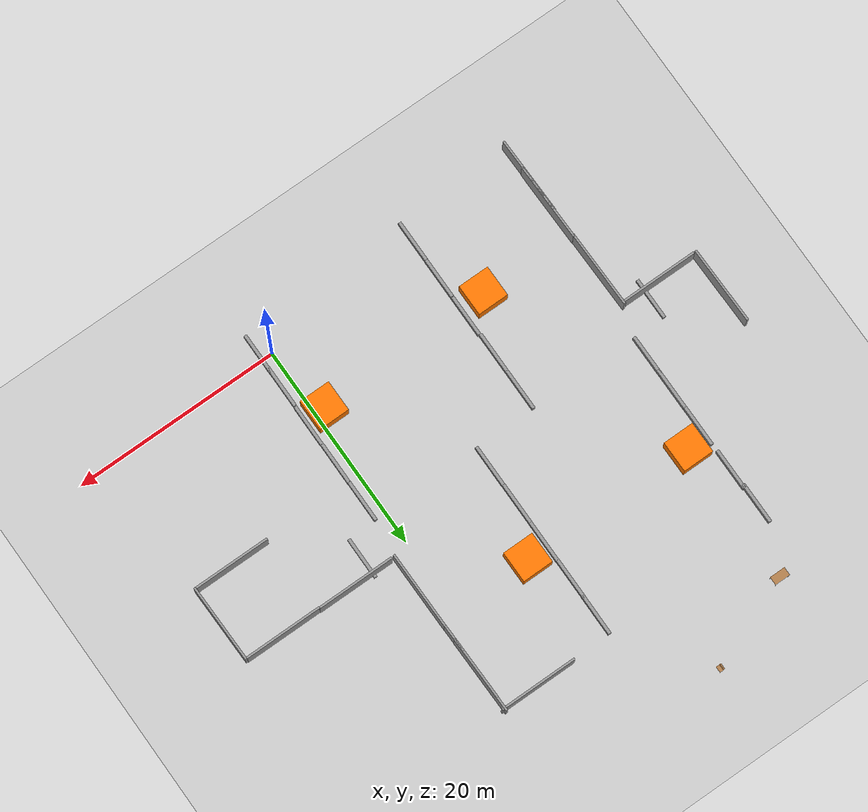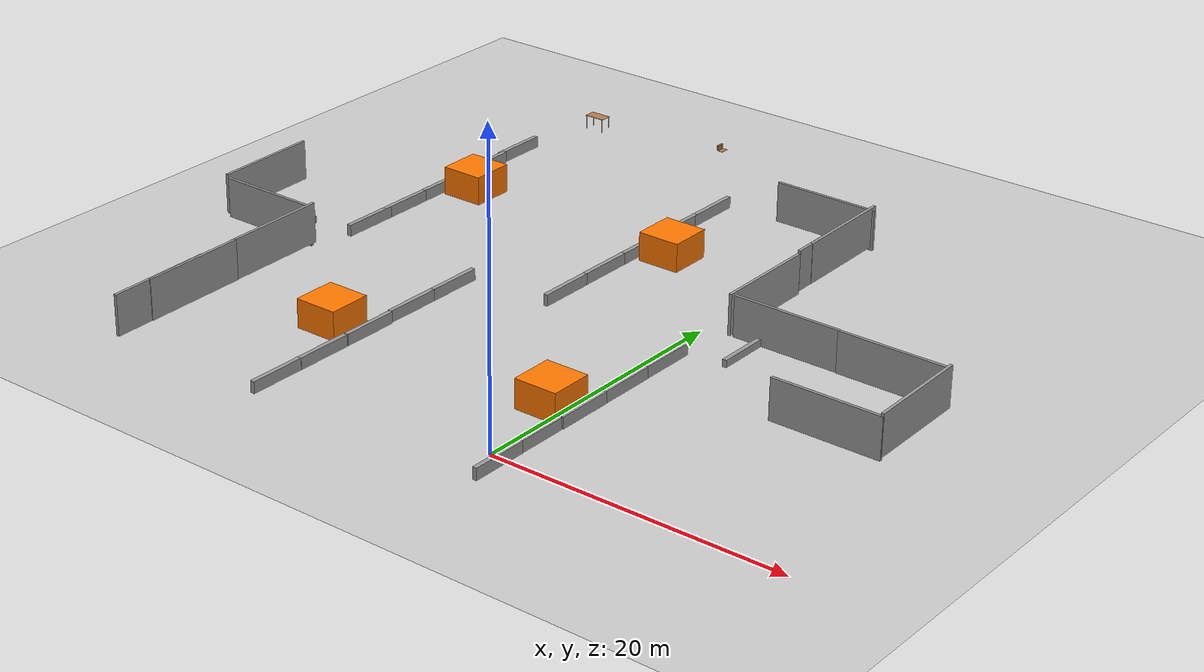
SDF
<sdf version="1.7">
 <world name="default">
  <light name="sun" type="directional">
   <pose>0 0 10 0 -0 0</pose>
   <diffuse>0.8 0.8 0.8 1</diffuse>
   <specular>0.2 0.2 0.2 1</specular>
   <attenuation>
    <range>1000</range>
    <constant>0.9</constant>
    <linear>0.01</linear>
    <quadratic>0.001</quadratic>
   </attenuation>
   <direction>-0.5 0.1 -0.9</direction>
   <spot><inner_angle>0</inner_angle><outer_angle>0</outer_angle><falloff>0</falloff></spot>
  </light>
  <model name="ground_plane">
   <static>1</static>
   <link name="link">
    <collision name="collision">
     <geometry><plane><normal>0 0 1</normal><size>100 100</size></plane></geometry>
     <surface><friction><ode><mu>100</mu><mu2>50</mu2></ode></friction></surface>
    </collision>
    <visual name="visual">
     <cast_shadows>0</cast_shadows>
     <geometry><plane><normal>0 0 1</normal><size>100 100</size></plane></geometry>
     <material>
      <script><uri>file://media/materials/scripts/gazebo.material</uri><name>Gazebo/Grey</name></script>
     </material>
    </visual>
   </link>
  </model>
  <gravity>0 0 -9.8</gravity>
  <magnetic_field>6e-06 2.3e-05 -4.2e-05</magnetic_field>
  <atmosphere type="adiabatic"/>
  <physics type="ode">
   <max_step_size>0.001</max_step_size>
   <real_time_factor>1</real_time_factor>
   <real_time_update_rate>1000</real_time_update_rate>
  </physics>
  <scene><ambient>0.4 0.4 0.4 1</ambient><background>0.7 0.7 0.7 1</background><shadows>1</shadows></scene>
  <audio><device>default</device></audio>
  <spherical_coordinates>
   <surface_model>EARTH_WGS84</surface_model>
   <latitude_deg>0</latitude_deg>
   <longitude_deg>0</longitude_deg>
   <elevation>0</elevation>
   <heading_deg>0</heading_deg>
  </spherical_coordinates>
  <model name="table">
   <static>1</static>
   <link name="link">
    <collision name="surface">
     <pose>0 0 1 0 -0 0</pose>
     <geometry><box><size>1.5 0.8 0.03</size></box></geometry>
     <surface><friction><ode><mu>0.6</mu><mu2>0.6</mu2></ode></friction></surface>
    </collision>
    <visual name="visual1">
     <pose>0 0 1 0 -0 0</pose>
     <geometry><box><size>1.5 0.8 0.03</size></box></geometry>
     <material>
      <script><uri>file://media/materials/scripts/gazebo.material</uri><name>Gazebo/Wood</name></script>
     </material>
    </visual>
    <collision name="front_left_leg">
     <pose>0.68 0.38 0.5 0 -0 0</pose>
     <geometry><cylinder><radius>0.02</radius><length>1</length></cylinder></geometry>
    </collision>
    <visual name="front_left_leg">
     <pose>0.68 0.38 0.5 0 -0 0</pose>
     <geometry><cylinder><radius>0.02</radius><length>1</length></cylinder></geometry>
     <material>
      <script><uri>file://media/materials/scripts/gazebo.material</uri><name>Gazebo/Grey</name></script>
     </material>
    </visual>
    <collision name="front_right_leg">
     <pose>0.68 -0.38 0.5 0 -0 0</pose>
     <geometry><cylinder><radius>0.02</radius><length>1</length></cylinder></geometry>
    </collision>
    <visual name="front_right_leg">
     <pose>0.68 -0.38 0.5 0 -0 0</pose>
     <geometry><cylinder><radius>0.02</radius><length>1</length></cylinder></geometry>
     <material>
      <script><uri>file://media/materials/scripts/gazebo.material</uri><name>Gazebo/Grey</name></script>
     </material>
    </visual>
    <collision name="back_right_leg">
     <pose>-0.68 -0.38 0.5 0 -0 0</pose>
     <geometry><cylinder><radius>0.02</radius><length>1</length></cylinder></geometry>
    </collision>
    <visual name="back_right_leg">
     <pose>-0.68 -0.38 0.5 0 -0 0</pose>
     <geometry><cylinder><radius>0.02</radius><length>1</length></cylinder></geometry>
     <material>
      <script><uri>file://media/materials/scripts/gazebo.material</uri><name>Gazebo/Grey</name></script>
     </material>
    </visual>
    <collision name="back_left_leg">
     <pose>-0.68 0.38 0.5 0 -0 0</pose>
     <geometry><cylinder><radius>0.02</radius><length>1</length></cylinder></geometry>
    </collision>
    <visual name="back_left_leg">
     <pose>-0.68 0.38 0.5 0 -0 0</pose>
     <geometry><cylinder><radius>0.02</radius><length>1</length></cylinder></geometry>
     <material>
      <script><uri>file://media/materials/scripts/gazebo.material</uri><name>Gazebo/Grey</name></script>
     </material>
    </visual>
   </link>
   <pose>-24.2186 40.8812 0.473539 0 -0 0</pose>
  </model>
  <model name="wooden_case">
   <link name="base">
    <pose>0 0 0.024 0 -0 0</pose>
    <inertial>
     <pose>-0.022184 0 0.171592 0 -0 0</pose>
     <mass>3.96264</mass>
     <inertia>
      <ixx>0.213536</ixx>
      <ixy>0</ixy>
      <ixz>0.000779377</ixz>
      <iyy>0.0708943</iyy>
      <iyz>0</iyz>
      <izz>0.154604</izz>
     </inertia>
    </inertial>
    <collision name="collision_back">
     <pose>-0.053975 0 0.1778 0 -0 0</pose>
     <geometry><box><size>0.01905 0.5461 0.3175</size></box></geometry>
     <surface>
      <contact>
       <poissons_ratio>0.347</poissons_ratio>
       <elastic_modulus>8.8e+09</elastic_modulus>
       <ode><kp>100000</kp><kd>100</kd><max_vel>100</max_vel><min_depth>0.001</min_depth></ode>
      </contact>
      <friction>
       <torsional>
        <coefficient>1</coefficient>
        <use_patch_radius>0</use_patch_radius>
        <surface_radius>0.01</surface_radius>
       </torsional>
      </friction>
     </surface>
    </collision>
    <visual name="visual_back">
     <pose>-0.053975 0 0.1778 0 -0 0</pose>
     <geometry><box><size>0.01905 0.5461 0.3175</size></box></geometry>
     <material>
      <script><uri>file://media/materials/scripts/gazebo.material</uri><name>Gazebo/Wood</name></script>
     </material>
    </visual>
    <collision name="collision_bottom">
     <pose>0 0 0.009525 0 -0 0</pose>
     <geometry><box><size>0.127 0.5842 0.01905</size></box></geometry>
     <surface>
      <contact>
       <poissons_ratio>0.347</poissons_ratio>
       <elastic_modulus>8.8e+09</elastic_modulus>
       <ode><kp>100000</kp><kd>100</kd><max_vel>100</max_vel><min_depth>0.001</min_depth></ode>
      </contact>
      <friction>
       <torsional>
        <coefficient>1</coefficient>
        <use_patch_radius>0</use_patch_radius>
        <surface_radius>0.01</surface_radius>
       </torsional>
      </friction>
     </surface>
    </collision>
    <visual name="visual_bottom">
     <pose>0 0 0.009525 0 -0 0</pose>
     <geometry><box><size>0.127 0.5842 0.01905</size></box></geometry>
     <material>
      <script><uri>file://media/materials/scripts/gazebo.material</uri><name>Gazebo/Wood</name></script>
     </material>
    </visual>
    <collision name="collision_top">
     <pose>0 0 0.346075 0 -0 0</pose>
     <geometry><box><size>0.127 0.5842 0.01905</size></box></geometry>
     <surface>
      <contact>
       <poissons_ratio>0.347</poissons_ratio>
       <elastic_modulus>8.8e+09</elastic_modulus>
       <ode><kp>100000</kp><kd>100</kd><max_vel>100</max_vel><min_depth>0.001</min_depth></ode>
      </contact>
      <friction>
       <torsional>
        <coefficient>1</coefficient>
        <use_patch_radius>0</use_patch_radius>
        <surface_radius>0.01</surface_radius>
       </torsional>
      </friction>
     </surface>
    </collision>
    <visual name="visual_top">
     <pose>0 0 0.346075 0 -0 0</pose>
     <geometry><box><size>0.127 0.5842 0.01905</size></box></geometry>
     <material>
      <script><uri>file://media/materials/scripts/gazebo.material</uri><name>Gazebo/Wood</name></script>
     </material>
    </visual>
    <collision name="collision_left">
     <pose>0 -0.282575 0.1778 0 -0 0</pose>
     <geometry><box><size>0.127 0.01905 0.3175</size></box></geometry>
     <surface>
      <contact>
       <poissons_ratio>0.347</poissons_ratio>
       <elastic_modulus>8.8e+09</elastic_modulus>
       <ode><kp>100000</kp><kd>100</kd><max_vel>100</max_vel><min_depth>0.001</min_depth></ode>
      </contact>
      <friction>
       <torsional>
        <coefficient>1</coefficient>
        <use_patch_radius>0</use_patch_radius>
        <surface_radius>0.01</surface_radius>
       </torsional>
      </friction>
     </surface>
    </collision>
    <visual name="visual_left">
     <pose>0 -0.282575 0.1778 0 -0 0</pose>
     <geometry><box><size>0.127 0.01905 0.3175</size></box></geometry>
     <material>
      <script><uri>file://media/materials/scripts/gazebo.material</uri><name>Gazebo/Wood</name></script>
     </material>
    </visual>
    <collision name="collision_right">
     <pose>0 0.282575 0.1778 0 -0 0</pose>
     <geometry><box><size>0.127 0.01905 0.3175</size></box></geometry>
     <surface>
      <contact>
       <poissons_ratio>0.347</poissons_ratio>
       <elastic_modulus>8.8e+09</elastic_modulus>
       <ode><kp>100000</kp><kd>100</kd><max_vel>100</max_vel><min_depth>0.001</min_depth></ode>
      </contact>
      <friction>
       <torsional>
        <coefficient>1</coefficient>
        <use_patch_radius>0</use_patch_radius>
        <surface_radius>0.01</surface_radius>
       </torsional>
      </friction>
     </surface>
    </collision>
    <visual name="visual_right">
     <pose>0 0.282575 0.1778 0 -0 0</pose>
     <geometry><box><size>0.127 0.01905 0.3175</size></box></geometry>
     <material>
      <script><uri>file://media/materials/scripts/gazebo.material</uri><name>Gazebo/Wood</name></script>
     </material>
    </visual>
    <collision name="collision_block_left">
     <pose>0.0095 -0.2151 -0.012 0 -0 0</pose>
     <geometry><box><size>0.108 0.05 0.024</size></box></geometry>
     <surface>
      <contact>
       <poissons_ratio>0.347</poissons_ratio>
       <elastic_modulus>8.8e+09</elastic_modulus>
       <ode><kp>100000</kp><kd>100</kd><max_vel>100</max_vel><min_depth>0.001</min_depth></ode>
      </contact>
      <friction>
       <torsional>
        <coefficient>1</coefficient>
        <use_patch_radius>0</use_patch_radius>
        <surface_radius>0.01</surface_radius>
       </torsional>
      </friction>
     </surface>
    </collision>
    <visual name="visual_block_left">
     <pose>0.0095 -0.2151 -0.012 0 -0 0</pose>
     <geometry><box><size>0.108 0.05 0.024</size></box></geometry>
     <material>
      <script><uri>file://media/materials/scripts/gazebo.material</uri><name>Gazebo/Wood</name></script>
     </material>
    </visual>
    <collision name="collision_block_right">
     <pose>0.0095 0.2151 -0.012 0 -0 0</pose>
     <geometry><box><size>0.108 0.05 0.024</size></box></geometry>
     <surface>
      <contact>
       <poissons_ratio>0.347</poissons_ratio>
       <elastic_modulus>8.8e+09</elastic_modulus>
       <ode><kp>100000</kp><kd>100</kd><max_vel>100</max_vel><min_depth>0.001</min_depth></ode>
      </contact>
      <friction>
       <torsional>
        <coefficient>1</coefficient>
        <use_patch_radius>0</use_patch_radius>
        <surface_radius>0.01</surface_radius>
       </torsional>
      </friction>
     </surface>
    </collision>
    <visual name="visual_block_right">
     <pose>0.0095 0.2151 -0.012 0 -0 0</pose>
     <geometry><box><size>0.108 0.05 0.024</size></box></geometry>
     <material>
      <script><uri>file://media/materials/scripts/gazebo.material</uri><name>Gazebo/Wood</name></script>
     </material>
    </visual>
   </link>
   <link name="lid">
    <pose>0.243775 0 0.009525 0 -0 0</pose>
    <inertial>
     <mass>1.97874</mass>
     <inertia>
      <ixx>0.0563367</ixx>
      <ixy>0</ixy>
      <ixz>0</ixz>
      <iyy>0.020911</iyy>
      <iyz>0</iyz>
      <izz>0.0771281</izz>
     </inertia>
    </inertial>
    <collision name="collision">
     <geometry><box><size>0.3556 0.5842 0.01905</size></box></geometry>
     <surface>
      <contact>
       <poissons_ratio>0.347</poissons_ratio>
       <elastic_modulus>8.8e+09</elastic_modulus>
       <ode><kp>100000</kp><kd>100</kd><max_vel>100</max_vel><min_depth>0.001</min_depth></ode>
      </contact>
      <friction>
       <torsional>
        <coefficient>1</coefficient>
        <use_patch_radius>0</use_patch_radius>
        <surface_radius>0.01</surface_radius>
       </torsional>
      </friction>
     </surface>
    </collision>
    <visual name="visual">
     <geometry><box><size>0.3556 0.5842 0.01905</size></box></geometry>
     <material>
      <script><uri>file://media/materials/scripts/gazebo.material</uri><name>Gazebo/Wood</name></script>
     </material>
    </visual>
    <visual name="tee_nut_1">
     <pose>0.122 -0.216 0 0 -0 0</pose>
     <geometry><cylinder><radius>0.00635</radius><length>0.0192405</length></cylinder></geometry>
     <material>
      <script><uri>file://media/materials/scripts/gazebo.material</uri><name>Gazebo/Grey</name></script>
     </material>
    </visual>
    <visual name="tee_nut_2">
     <pose>0.122 -0.088 0 0 -0 0</pose>
     <geometry><cylinder><radius>0.00635</radius><length>0.0192405</length></cylinder></geometry>
     <material>
      <script><uri>file://media/materials/scripts/gazebo.material</uri><name>Gazebo/Grey</name></script>
     </material>
    </visual>
    <visual name="tee_nut_3">
     <pose>0.122 0.088 0 0 -0 0</pose>
     <geometry><cylinder><radius>0.00635</radius><length>0.0192405</length></cylinder></geometry>
     <material>
      <script><uri>file://media/materials/scripts/gazebo.material</uri><name>Gazebo/Grey</name></script>
     </material>
    </visual>
    <visual name="tee_nut_4">
     <pose>0.122 0.216 0 0 -0 0</pose>
     <geometry><cylinder><radius>0.00635</radius><length>0.0192405</length></cylinder></geometry>
     <material>
      <script><uri>file://media/materials/scripts/gazebo.material</uri><name>Gazebo/Grey</name></script>
     </material>
    </visual>
   </link>
   <joint name="lid_hinge" type="revolute">
    <pose>-0.1778 0 0.01905 0 -0 0</pose>
    <parent>base</parent>
    <child>lid</child>
    <axis>
     <xyz>0 1 0</xyz>
     <limit><upper>0.523599</upper><lower>-1.5708</lower></limit>
     <dynamics><spring_reference>0</spring_reference><spring_stiffness>0</spring_stiffness></dynamics>
    </axis>
   </joint>
   <pose>-15.8267 44.2683 -0.001057 0 -0.000429 0</pose>
  </model>
  <model name="factory_machines">
   <link name="link_0">
    <inertial>
     <mass>1</mass>
     <inertia>
      <ixx>0.166667</ixx>
      <ixy>0</ixy>
      <ixz>0</ixz>
      <iyy>0.166667</iyy>
      <iyz>0</iyz>
      <izz>0.166667</izz>
     </inertia>
    </inertial>
    <pose>5.10465 10.3846 0 0 -0 0</pose>
    <visual name="visual">
     <geometry><box><size>3 3 2</size></box></geometry>
     <material>
      <lighting>1</lighting>
      <script><uri>file://media/materials/scripts/gazebo.material</uri><name>Gazebo/Grey</name></script>
      <shader type="pixel"><normal_map>__default__</normal_map></shader>
      <ambient>1 0.471 0 1</ambient>
      <diffuse>0.7 0.7 0.7 1</diffuse>
      <specular>0.01 0.01 0.01 1</specular>
      <emissive>0 0 0 1</emissive>
     </material>
    </visual>
    <collision name="collision">
     <geometry><box><size>3 3 2</size></box></geometry>
     <surface>
      <friction>
       <ode><mu>1</mu><mu2>1</mu2><fdir1>0 0 0</fdir1><slip1>0</slip1><slip2>0</slip2></ode>
       <torsional>
        <coefficient>1</coefficient>
        <patch_radius>0</patch_radius>
        <surface_radius>0</surface_radius>
        <use_patch_radius>1</use_patch_radius>
        <ode><slip>0</slip></ode>
       </torsional>
      </friction>
      <bounce><restitution_coefficient>0</restitution_coefficient><threshold>1e+06</threshold></bounce>
      <contact>
       <collide_without_contact>0</collide_without_contact>
       <collide_without_contact_bitmask>1</collide_without_contact_bitmask>
       <collide_bitmask>1</collide_bitmask>
       <ode>
        <soft_cfm>0</soft_cfm>
        <soft_erp>0.2</soft_erp>
        <kp>1e+13</kp>
        <kd>1</kd>
        <max_vel>0.01</max_vel>
        <min_depth>0</min_depth>
       </ode>
       <bullet>
        <split_impulse>1</split_impulse>
        <split_impulse_penetration_threshold>-0.01</split_impulse_penetration_threshold>
        <soft_cfm>0</soft_cfm>
        <soft_erp>0.2</soft_erp>
        <kp>1e+13</kp>
        <kd>1</kd>
       </bullet>
      </contact>
     </surface>
    </collision>
   </link>
   <link name="link_0_clone">
    <inertial>
     <mass>1</mass>
     <inertia>
      <ixx>0.166667</ixx>
      <ixy>0</ixy>
      <ixz>0</ixz>
      <iyy>0.166667</iyy>
      <iyz>0</iyz>
      <izz>0.166667</izz>
     </inertia>
    </inertial>
    <pose>11.7 -10.343 0 0 -0 0</pose>
    <visual name="visual">
     <geometry><box><size>3 3 2</size></box></geometry>
     <material>
      <lighting>1</lighting>
      <script><uri>file://media/materials/scripts/gazebo.material</uri><name>Gazebo/Grey</name></script>
      <shader type="pixel"><normal_map>__default__</normal_map></shader>
      <ambient>1 0.471 0 1</ambient>
      <diffuse>0.7 0.7 0.7 1</diffuse>
      <specular>0.01 0.01 0.01 1</specular>
      <emissive>0 0 0 1</emissive>
     </material>
    </visual>
    <collision name="collision">
     <geometry><box><size>3 3 2</size></box></geometry>
     <surface>
      <friction>
       <ode><mu>1</mu><mu2>1</mu2><fdir1>0 0 0</fdir1><slip1>0</slip1><slip2>0</slip2></ode>
       <torsional>
        <coefficient>1</coefficient>
        <patch_radius>0</patch_radius>
        <surface_radius>0</surface_radius>
        <use_patch_radius>1</use_patch_radius>
        <ode><slip>0</slip></ode>
       </torsional>
      </friction>
      <bounce><restitution_coefficient>0</restitution_coefficient><threshold>1e+06</threshold></bounce>
      <contact>
       <collide_without_contact>0</collide_without_contact>
       <collide_without_contact_bitmask>1</collide_without_contact_bitmask>
       <collide_bitmask>1</collide_bitmask>
       <ode>
        <soft_cfm>0</soft_cfm>
        <soft_erp>0.2</soft_erp>
        <kp>1e+13</kp>
        <kd>1</kd>
        <max_vel>0.01</max_vel>
        <min_depth>0</min_depth>
       </ode>
       <bullet>
        <split_impulse>1</split_impulse>
        <split_impulse_penetration_threshold>-0.01</split_impulse_penetration_threshold>
        <soft_cfm>0</soft_cfm>
        <soft_erp>0.2</soft_erp>
        <kp>1e+13</kp>
        <kd>1</kd>
       </bullet>
      </contact>
     </surface>
    </collision>
   </link>
   <link name="link_0_clone_0">
    <inertial>
     <mass>1</mass>
     <inertia>
      <ixx>0.166667</ixx>
      <ixy>0</ixy>
      <ixz>0</ixz>
      <iyy>0.166667</iyy>
      <iyz>0</iyz>
      <izz>0.166667</izz>
     </inertia>
    </inertial>
    <pose>-5.21258 -10.6315 0 0 -0 0</pose>
    <visual name="visual">
     <geometry><box><size>3 3 2</size></box></geometry>
     <material>
      <lighting>1</lighting>
      <script><uri>file://media/materials/scripts/gazebo.material</uri><name>Gazebo/Grey</name></script>
      <shader type="pixel"><normal_map>__default__</normal_map></shader>
      <ambient>1 0.471 0 1</ambient>
      <diffuse>0.7 0.7 0.7 1</diffuse>
      <specular>0.01 0.01 0.01 1</specular>
      <emissive>0 0 0 1</emissive>
     </material>
    </visual>
    <collision name="collision">
     <geometry><box><size>3 3 2</size></box></geometry>
     <surface>
      <friction>
       <ode><mu>1</mu><mu2>1</mu2><fdir1>0 0 0</fdir1><slip1>0</slip1><slip2>0</slip2></ode>
       <torsional>
        <coefficient>1</coefficient>
        <patch_radius>0</patch_radius>
        <surface_radius>0</surface_radius>
        <use_patch_radius>1</use_patch_radius>
        <ode><slip>0</slip></ode>
       </torsional>
      </friction>
      <bounce><restitution_coefficient>0</restitution_coefficient><threshold>1e+06</threshold></bounce>
      <contact>
       <collide_without_contact>0</collide_without_contact>
       <collide_without_contact_bitmask>1</collide_without_contact_bitmask>
       <collide_bitmask>1</collide_bitmask>
       <ode>
        <soft_cfm>0</soft_cfm>
        <soft_erp>0.2</soft_erp>
        <kp>1e+13</kp>
        <kd>1</kd>
        <max_vel>0.01</max_vel>
        <min_depth>0</min_depth>
       </ode>
       <bullet>
        <split_impulse>1</split_impulse>
        <split_impulse_penetration_threshold>-0.01</split_impulse_penetration_threshold>
        <soft_cfm>0</soft_cfm>
        <soft_erp>0.2</soft_erp>
        <kp>1e+13</kp>
        <kd>1</kd>
       </bullet>
      </contact>
     </surface>
    </collision>
   </link>
   <link name="link_0_clone_1">
    <inertial>
     <mass>1</mass>
     <inertia>
      <ixx>0.166667</ixx>
      <ixy>0</ixy>
      <ixz>0</ixz>
      <iyy>0.166667</iyy>
      <iyz>0</iyz>
      <izz>0.166667</izz>
     </inertia>
    </inertial>
    <pose>-11.592 10.59 0 0 -0 0</pose>
    <visual name="visual">
     <geometry><box><size>3 3 2</size></box></geometry>
     <material>
      <lighting>1</lighting>
      <script><uri>file://media/materials/scripts/gazebo.material</uri><name>Gazebo/Grey</name></script>
      <shader type="pixel"><normal_map>__default__</normal_map></shader>
      <ambient>1 0.471 0 1</ambient>
      <diffuse>0.7 0.7 0.7 1</diffuse>
      <specular>0.01 0.01 0.01 1</specular>
      <emissive>0 0 0 1</emissive>
     </material>
    </visual>
    <collision name="collision">
     <geometry><box><size>3 3 2</size></box></geometry>
     <surface>
      <friction>
       <ode><mu>1</mu><mu2>1</mu2><fdir1>0 0 0</fdir1><slip1>0</slip1><slip2>0</slip2></ode>
       <torsional>
        <coefficient>1</coefficient>
        <patch_radius>0</patch_radius>
        <surface_radius>0</surface_radius>
        <use_patch_radius>1</use_patch_radius>
        <ode><slip>0</slip></ode>
       </torsional>
      </friction>
      <bounce><restitution_coefficient>0</restitution_coefficient><threshold>1e+06</threshold></bounce>
      <contact>
       <collide_without_contact>0</collide_without_contact>
       <collide_without_contact_bitmask>1</collide_without_contact_bitmask>
       <collide_bitmask>1</collide_bitmask>
       <ode>
        <soft_cfm>0</soft_cfm>
        <soft_erp>0.2</soft_erp>
        <kp>1e+13</kp>
        <kd>1</kd>
        <max_vel>0.01</max_vel>
        <min_depth>0</min_depth>
       </ode>
       <bullet>
        <split_impulse>1</split_impulse>
        <split_impulse_penetration_threshold>-0.01</split_impulse_penetration_threshold>
        <soft_cfm>0</soft_cfm>
        <soft_erp>0.2</soft_erp>
        <kp>1e+13</kp>
        <kd>1</kd>
       </bullet>
      </contact>
     </surface>
    </collision>
   </link>
   <static>0</static>
   <pose>-12.6539 16.8628 0.999939 -0 -9e-06 0.003009</pose>
  </model>
  <model name="grey_wall">
   <static>1</static>
   <link name="link">
    <pose>0 0 1.4 0 -0 0</pose>
    <collision name="collision"><geometry><box><size>7.5 0.2 2.8</size></box></geometry></collision>
    <visual name="visual">
     <cast_shadows>0</cast_shadows>
     <geometry><box><size>7.5 0.2 2.8</size></box></geometry>
     <material>
      <script>
       <uri>model://grey_wall/materials/scripts</uri>
       <uri>model://grey_wall/materials/textures</uri>
       <name>vrc/grey_wall</name>
      </script>
     </material>
    </visual>
   </link>
   <pose>1.65384 24.3462 0 0 0 -1.56374</pose>
  </model>
  <model name="grey_wall_0">
   <static>1</static>
   <link name="link">
    <pose>0 0 1.4 0 -0 0</pose>
    <collision name="collision"><geometry><box><size>7.5 0.2 2.8</size></box></geometry></collision>
    <visual name="visual">
     <cast_shadows>0</cast_shadows>
     <geometry><box><size>7.5 0.2 2.8</size></box></geometry>
     <material>
      <script>
       <uri>model://grey_wall/materials/scripts</uri>
       <uri>model://grey_wall/materials/textures</uri>
       <name>vrc/grey_wall</name>
      </script>
     </material>
    </visual>
   </link>
   <pose>5.71873 20.6971 0 0 -0 0</pose>
  </model>
  <model name="grey_wall_1">
   <static>1</static>
   <link name="link">
    <pose>0 0 1.4 0 -0 0</pose>
    <collision name="collision"><geometry><box><size>7.5 0.2 2.8</size></box></geometry></collision>
    <visual name="visual">
     <cast_shadows>0</cast_shadows>
     <geometry><box><size>7.5 0.2 2.8</size></box></geometry>
     <material>
      <script>
       <uri>model://grey_wall/materials/scripts</uri>
       <uri>model://grey_wall/materials/textures</uri>
       <name>vrc/grey_wall</name>
      </script>
     </material>
    </visual>
   </link>
   <pose>1.57168 31.856 0.19567 0 0 -1.55567</pose>
  </model>
  <model name="grey_wall_1_clone">
   <static>1</static>
   <link name="link">
    <pose>0 0 1.4 0 -0 0</pose>
    <collision name="collision"><geometry><box><size>7.5 0.2 2.8</size></box></geometry></collision>
    <visual name="visual">
     <cast_shadows>0</cast_shadows>
     <geometry><box><size>7.5 0.2 2.8</size></box></geometry>
     <material>
      <script>
       <uri>model://grey_wall/materials/scripts</uri>
       <uri>model://grey_wall/materials/textures</uri>
       <name>vrc/grey_wall</name>
      </script>
     </material>
    </visual>
   </link>
   <pose>17.0679 16.9633 0.19567 0 0 -1.55567</pose>
  </model>
  <model name="grey_wall_0_clone">
   <static>1</static>
   <link name="link">
    <pose>0 0 1.4 0 -0 0</pose>
    <collision name="collision"><geometry><box><size>7.5 0.2 2.8</size></box></geometry></collision>
    <visual name="visual">
     <cast_shadows>0</cast_shadows>
     <geometry><box><size>7.5 0.2 2.8</size></box></geometry>
     <material>
      <script>
       <uri>model://grey_wall/materials/scripts</uri>
       <uri>model://grey_wall/materials/textures</uri>
       <name>vrc/grey_wall</name>
      </script>
     </material>
    </visual>
   </link>
   <pose>-1.96273 36.6456 0 0 -0 0</pose>
  </model>
  <model name="grey_wall_0_clone_0">
   <static>1</static>
   <link name="link">
    <pose>0 0 1.4 0 -0 0</pose>
    <collision name="collision"><geometry><box><size>7.5 0.2 2.8</size></box></geometry></collision>
    <visual name="visual">
     <cast_shadows>0</cast_shadows>
     <geometry><box><size>7.5 0.2 2.8</size></box></geometry>
     <material>
      <script>
       <uri>model://grey_wall/materials/scripts</uri>
       <uri>model://grey_wall/materials/textures</uri>
       <name>vrc/grey_wall</name>
      </script>
     </material>
    </visual>
   </link>
   <pose>13.1639 20.6474 0 0 -0 0</pose>
  </model>
  <model name="grey_wall_0_clone_1">
   <static>1</static>
   <link name="link">
    <pose>0 0 1.4 0 -0 0</pose>
    <collision name="collision"><geometry><box><size>7.5 0.2 2.8</size></box></geometry></collision>
    <visual name="visual">
     <cast_shadows>0</cast_shadows>
     <geometry><box><size>7.5 0.2 2.8</size></box></geometry>
     <material>
      <script>
       <uri>model://grey_wall/materials/scripts</uri>
       <uri>model://grey_wall/materials/textures</uri>
       <name>vrc/grey_wall</name>
      </script>
     </material>
    </visual>
   </link>
   <pose>13.4269 13.2768 0 0 -0 0</pose>
  </model>
  <model name="grey_wall_1_clone_0">
   <static>1</static>
   <link name="link">
    <pose>0 0 1.4 0 -0 0</pose>
    <collision name="collision"><geometry><box><size>7.5 0.2 2.8</size></box></geometry></collision>
    <visual name="visual">
     <cast_shadows>0</cast_shadows>
     <geometry><box><size>7.5 0.2 2.8</size></box></geometry>
     <material>
      <script>
       <uri>model://grey_wall/materials/scripts</uri>
       <uri>model://grey_wall/materials/textures</uri>
       <name>vrc/grey_wall</name>
      </script>
     </material>
    </visual>
   </link>
   <pose>1.57176 33.2174 0.19567 0 0 -1.55567</pose>
  </model>
  <model name="grey_wall_1_clone_clone">
   <static>1</static>
   <link name="link">
    <pose>0 0 1.4 0 -0 0</pose>
    <collision name="collision"><geometry><box><size>7.5 0.2 2.8</size></box></geometry></collision>
    <visual name="visual">
     <cast_shadows>0</cast_shadows>
     <geometry><box><size>7.5 0.2 2.8</size></box></geometry>
     <material>
      <script>
       <uri>model://grey_wall/materials/scripts</uri>
       <uri>model://grey_wall/materials/textures</uri>
       <name>vrc/grey_wall</name>
      </script>
     </material>
    </visual>
   </link>
   <pose>-26.9144 10.5164 0.19567 0 0 -1.55567</pose>
  </model>
  <model name="grey_wall_1_clone_clone_0">
   <static>1</static>
   <link name="link">
    <pose>0 0 1.4 0 -0 0</pose>
    <collision name="collision"><geometry><box><size>7.5 0.2 2.8</size></box></geometry></collision>
    <visual name="visual">
     <cast_shadows>0</cast_shadows>
     <geometry><box><size>7.5 0.2 2.8</size></box></geometry>
     <material>
      <script>
       <uri>model://grey_wall/materials/scripts</uri>
       <uri>model://grey_wall/materials/textures</uri>
       <name>vrc/grey_wall</name>
      </script>
     </material>
    </visual>
   </link>
   <pose>-26.7681 3.21616 0.19567 0 0 -1.55567</pose>
  </model>
  <model name="grey_wall_1_clone_clone_1">
   <static>1</static>
   <link name="link">
    <pose>0 0 1.4 0 -0 0</pose>
    <collision name="collision"><geometry><box><size>7.5 0.2 2.8</size></box></geometry></collision>
    <visual name="visual">
     <cast_shadows>0</cast_shadows>
     <geometry><box><size>7.5 0.2 2.8</size></box></geometry>
     <material>
      <script>
       <uri>model://grey_wall/materials/scripts</uri>
       <uri>model://grey_wall/materials/textures</uri>
       <name>vrc/grey_wall</name>
      </script>
     </material>
    </visual>
   </link>
   <pose>-26.7715 0.421848 0.19567 0 0 -1.55567</pose>
  </model>
  <model name="grey_wall_0_clone_0_clone">
   <static>1</static>
   <link name="link">
    <pose>0 0 1.4 0 -0 0</pose>
    <collision name="collision"><geometry><box><size>7.5 0.2 2.8</size></box></geometry></collision>
    <visual name="visual">
     <cast_shadows>0</cast_shadows>
     <geometry><box><size>7.5 0.2 2.8</size></box></geometry>
     <material>
      <script>
       <uri>model://grey_wall/materials/scripts</uri>
       <uri>model://grey_wall/materials/textures</uri>
       <name>vrc/grey_wall</name>
      </script>
     </material>
    </visual>
   </link>
   <pose>-30.6989 14.0157 0 0 -0 0</pose>
  </model>
  <model name="grey_wall_1_clone_clone_1_clone">
   <static>1</static>
   <link name="link">
    <pose>0 0 1.4 0 -0 0</pose>
    <collision name="collision"><geometry><box><size>7.5 0.2 2.8</size></box></geometry></collision>
    <visual name="visual">
     <cast_shadows>0</cast_shadows>
     <geometry><box><size>7.5 0.2 2.8</size></box></geometry>
     <material>
      <script>
       <uri>model://grey_wall/materials/scripts</uri>
       <uri>model://grey_wall/materials/textures</uri>
       <name>vrc/grey_wall</name>
      </script>
     </material>
    </visual>
   </link>
   <pose>-34.6805 17.7285 0.19567 0 0 -1.55567</pose>
  </model>
  <model name="conveyor_fill">
   <link name="link">
    <inertial>
     <mass>1</mass>
     <inertia>
      <ixx>0.166667</ixx>
      <ixy>0</ixy>
      <ixz>0</ixz>
      <iyy>0.166667</iyy>
      <iyz>0</iyz>
      <izz>0.166667</izz>
     </inertia>
    </inertial>
    <pose>0 0 -0.277043 0 -0 0</pose>
    <visual name="visual">
     <geometry><box><size>0.3 4 0.5</size></box></geometry>
     <material>
      <script><name>Gazebo/Grey</name><uri>file://media/materials/scripts/gazebo.material</uri></script>
      <shader type="pixel"><normal_map>__default__</normal_map></shader>
      <ambient>0.3 0.3 0.3 1</ambient>
      <diffuse>0.7 0.7 0.7 1</diffuse>
      <specular>0.01 0.01 0.01 1</specular>
      <emissive>0 0 0 1</emissive>
     </material>
    </visual>
    <collision name="collision">
     <geometry><box><size>0.3 4 0.5</size></box></geometry>
     <surface>
      <friction>
       <ode><mu>1</mu><mu2>1</mu2><fdir1>0 0 0</fdir1><slip1>0</slip1><slip2>0</slip2></ode>
       <torsional>
        <coefficient>1</coefficient>
        <patch_radius>0</patch_radius>
        <surface_radius>0</surface_radius>
        <use_patch_radius>1</use_patch_radius>
        <ode><slip>0</slip></ode>
       </torsional>
      </friction>
      <bounce><restitution_coefficient>0</restitution_coefficient><threshold>1e+06</threshold></bounce>
      <contact>
       <collide_without_contact>0</collide_without_contact>
       <collide_without_contact_bitmask>1</collide_without_contact_bitmask>
       <collide_bitmask>1</collide_bitmask>
       <ode>
        <soft_cfm>0</soft_cfm>
        <soft_erp>0.2</soft_erp>
        <kp>1e+13</kp>
        <kd>1</kd>
        <max_vel>0.01</max_vel>
        <min_depth>0</min_depth>
       </ode>
       <bullet>
        <split_impulse>1</split_impulse>
        <split_impulse_penetration_threshold>-0.01</split_impulse_penetration_threshold>
        <soft_cfm>0</soft_cfm>
        <soft_erp>0.2</soft_erp>
        <kp>1e+13</kp>
        <kd>1</kd>
       </bullet>
      </contact>
     </surface>
    </collision>
   </link>
   <static>0</static>
   <pose>3.87789 19.029 0.5 0 0 -0.00195</pose>
  </model>
  <model name="conveyor_fill_taller">
   <link name="link">
    <inertial>
     <mass>1</mass>
     <inertia>
      <ixx>0.166667</ixx>
      <ixy>0</ixy>
      <ixz>0</ixz>
      <iyy>0.166667</iyy>
      <iyz>0</iyz>
      <izz>0.166667</izz>
     </inertia>
    </inertial>
    <pose>0 0 -0.277043 0 -0 0</pose>
    <visual name="visual">
     <geometry><box><size>0.3 4 1</size></box></geometry>
     <material>
      <script><name>Gazebo/Grey</name><uri>file://media/materials/scripts/gazebo.material</uri></script>
      <shader type="pixel"><normal_map>__default__</normal_map></shader>
      <ambient>0.3 0.3 0.3 1</ambient>
      <diffuse>0.7 0.7 0.7 1</diffuse>
      <specular>0.01 0.01 0.01 1</specular>
      <emissive>0 0 0 1</emissive>
     </material>
    </visual>
    <collision name="collision">
     <geometry><box><size>0.3 4 1</size></box></geometry>
     <surface>
      <friction>
       <ode><mu>1</mu><mu2>1</mu2><fdir1>0 0 0</fdir1><slip1>0</slip1><slip2>0</slip2></ode>
       <torsional>
        <coefficient>1</coefficient>
        <patch_radius>0</patch_radius>
        <surface_radius>0</surface_radius>
        <use_patch_radius>1</use_patch_radius>
        <ode><slip>0</slip></ode>
       </torsional>
      </friction>
      <bounce><restitution_coefficient>0</restitution_coefficient><threshold>1e+06</threshold></bounce>
      <contact>
       <collide_without_contact>0</collide_without_contact>
       <collide_without_contact_bitmask>1</collide_without_contact_bitmask>
       <collide_bitmask>1</collide_bitmask>
       <ode>
        <soft_cfm>0</soft_cfm>
        <soft_erp>0.2</soft_erp>
        <kp>1e+13</kp>
        <kd>1</kd>
        <max_vel>0.01</max_vel>
        <min_depth>0</min_depth>
       </ode>
       <bullet>
        <split_impulse>1</split_impulse>
        <split_impulse_penetration_threshold>-0.01</split_impulse_penetration_threshold>
        <soft_cfm>0</soft_cfm>
        <soft_erp>0.2</soft_erp>
        <kp>1e+13</kp>
        <kd>1</kd>
       </bullet>
      </contact>
     </surface>
    </collision>
   </link>
   <static>0</static>
   <pose>1.04516 15.0369 0.5 0 0 -0.00195</pose>
  </model>
  <model name="conveyor_fill_taller_clone">
   <link name="link">
    <inertial>
     <mass>1</mass>
     <inertia>
      <ixx>0.166667</ixx>
      <ixy>0</ixy>
      <ixz>0</ixz>
      <iyy>0.166667</iyy>
      <iyz>0</iyz>
      <izz>0.166667</izz>
     </inertia>
    </inertial>
    <pose>0 0 -0.277043 0 -0 0</pose>
    <visual name="visual">
     <geometry><box><size>0.3 4 1</size></box></geometry>
     <material>
      <script><name>Gazebo/Grey</name><uri>file://media/materials/scripts/gazebo.material</uri></script>
      <shader type="pixel"><normal_map>__default__</normal_map></shader>
      <ambient>0.3 0.3 0.3 1</ambient>
      <diffuse>0.7 0.7 0.7 1</diffuse>
      <specular>0.01 0.01 0.01 1</specular>
      <emissive>0 0 0 1</emissive>
     </material>
    </visual>
    <collision name="collision">
     <geometry><box><size>0.3 4 1</size></box></geometry>
     <surface>
      <friction>
       <ode><mu>1</mu><mu2>1</mu2><fdir1>0 0 0</fdir1><slip1>0</slip1><slip2>0</slip2></ode>
       <torsional>
        <coefficient>1</coefficient>
        <patch_radius>0</patch_radius>
        <surface_radius>0</surface_radius>
        <use_patch_radius>1</use_patch_radius>
        <ode><slip>0</slip></ode>
       </torsional>
      </friction>
      <bounce><restitution_coefficient>0</restitution_coefficient><threshold>1e+06</threshold></bounce>
      <contact>
       <collide_without_contact>0</collide_without_contact>
       <collide_without_contact_bitmask>1</collide_without_contact_bitmask>
       <collide_bitmask>1</collide_bitmask>
       <ode>
        <soft_cfm>0</soft_cfm>
        <soft_erp>0.2</soft_erp>
        <kp>1e+13</kp>
        <kd>1</kd>
        <max_vel>0.01</max_vel>
        <min_depth>0</min_depth>
       </ode>
       <bullet>
        <split_impulse>1</split_impulse>
        <split_impulse_penetration_threshold>-0.01</split_impulse_penetration_threshold>
        <soft_cfm>0</soft_cfm>
        <soft_erp>0.2</soft_erp>
        <kp>1e+13</kp>
        <kd>1</kd>
       </bullet>
      </contact>
     </surface>
    </collision>
   </link>
   <static>0</static>
   <pose>1.05424 11.0232 0.5 0 0 -0.00195</pose>
  </model>
  <model name="conveyor_fill_taller_clone_0">
   <link name="link">
    <inertial>
     <mass>1</mass>
     <inertia>
      <ixx>0.166667</ixx>
      <ixy>0</ixy>
      <ixz>0</ixz>
      <iyy>0.166667</iyy>
      <iyz>0</iyz>
      <izz>0.166667</izz>
     </inertia>
    </inertial>
    <pose>0 0 -0.277043 0 -0 0</pose>
    <visual name="visual">
     <geometry><box><size>0.3 4 1</size></box></geometry>
     <material>
      <script><name>Gazebo/Grey</name><uri>file://media/materials/scripts/gazebo.material</uri></script>
      <shader type="pixel"><normal_map>__default__</normal_map></shader>
      <ambient>0.3 0.3 0.3 1</ambient>
      <diffuse>0.7 0.7 0.7 1</diffuse>
      <specular>0.01 0.01 0.01 1</specular>
      <emissive>0 0 0 1</emissive>
     </material>
    </visual>
    <collision name="collision">
     <geometry><box><size>0.3 4 1</size></box></geometry>
     <surface>
      <friction>
       <ode><mu>1</mu><mu2>1</mu2><fdir1>0 0 0</fdir1><slip1>0</slip1><slip2>0</slip2></ode>
       <torsional>
        <coefficient>1</coefficient>
        <patch_radius>0</patch_radius>
        <surface_radius>0</surface_radius>
        <use_patch_radius>1</use_patch_radius>
        <ode><slip>0</slip></ode>
       </torsional>
      </friction>
      <bounce><restitution_coefficient>0</restitution_coefficient><threshold>1e+06</threshold></bounce>
      <contact>
       <collide_without_contact>0</collide_without_contact>
       <collide_without_contact_bitmask>1</collide_without_contact_bitmask>
       <collide_bitmask>1</collide_bitmask>
       <ode>
        <soft_cfm>0</soft_cfm>
        <soft_erp>0.2</soft_erp>
        <kp>1e+13</kp>
        <kd>1</kd>
        <max_vel>0.01</max_vel>
        <min_depth>0</min_depth>
       </ode>
       <bullet>
        <split_impulse>1</split_impulse>
        <split_impulse_penetration_threshold>-0.01</split_impulse_penetration_threshold>
        <soft_cfm>0</soft_cfm>
        <soft_erp>0.2</soft_erp>
        <kp>1e+13</kp>
        <kd>1</kd>
       </bullet>
      </contact>
     </surface>
    </collision>
   </link>
   <static>0</static>
   <pose>1.06589 7.00669 0.5 0 0 -0.00195</pose>
  </model>
  <model name="conveyor_fill_taller_clone_1">
   <link name="link">
    <inertial>
     <mass>1</mass>
     <inertia>
      <ixx>0.166667</ixx>
      <ixy>0</ixy>
      <ixz>0</ixz>
      <iyy>0.166667</iyy>
      <iyz>0</iyz>
      <izz>0.166667</izz>
     </inertia>
    </inertial>
    <pose>0 0 -0.277043 0 -0 0</pose>
    <visual name="visual">
     <geometry><box><size>0.3 4 1</size></box></geometry>
     <material>
      <script><name>Gazebo/Grey</name><uri>file://media/materials/scripts/gazebo.material</uri></script>
      <shader type="pixel"><normal_map>__default__</normal_map></shader>
      <ambient>0.3 0.3 0.3 1</ambient>
      <diffuse>0.7 0.7 0.7 1</diffuse>
      <specular>0.01 0.01 0.01 1</specular>
      <emissive>0 0 0 1</emissive>
     </material>
    </visual>
    <collision name="collision">
     <geometry><box><size>0.3 4 1</size></box></geometry>
     <surface>
      <friction>
       <ode><mu>1</mu><mu2>1</mu2><fdir1>0 0 0</fdir1><slip1>0</slip1><slip2>0</slip2></ode>
       <torsional>
        <coefficient>1</coefficient>
        <patch_radius>0</patch_radius>
        <surface_radius>0</surface_radius>
        <use_patch_radius>1</use_patch_radius>
        <ode><slip>0</slip></ode>
       </torsional>
      </friction>
      <bounce><restitution_coefficient>0</restitution_coefficient><threshold>1e+06</threshold></bounce>
      <contact>
       <collide_without_contact>0</collide_without_contact>
       <collide_without_contact_bitmask>1</collide_without_contact_bitmask>
       <collide_bitmask>1</collide_bitmask>
       <ode>
        <soft_cfm>0</soft_cfm>
        <soft_erp>0.2</soft_erp>
        <kp>1e+13</kp>
        <kd>1</kd>
        <max_vel>0.01</max_vel>
        <min_depth>0</min_depth>
       </ode>
       <bullet>
        <split_impulse>1</split_impulse>
        <split_impulse_penetration_threshold>-0.01</split_impulse_penetration_threshold>
        <soft_cfm>0</soft_cfm>
        <soft_erp>0.2</soft_erp>
        <kp>1e+13</kp>
        <kd>1</kd>
       </bullet>
      </contact>
     </surface>
    </collision>
   </link>
   <static>0</static>
   <pose>1.02367 2.91712 0.5 0 0 -0.00195</pose>
  </model>
  <model name="conveyor_fill_taller_clone_2">
   <link name="link">
    <inertial>
     <mass>1</mass>
     <inertia>
      <ixx>0.166667</ixx>
      <ixy>0</ixy>
      <ixz>0</ixz>
      <iyy>0.166667</iyy>
      <iyz>0</iyz>
      <izz>0.166667</izz>
     </inertia>
    </inertial>
    <pose>0 0 -0.277043 0 -0 0</pose>
    <visual name="visual">
     <geometry><box><size>0.3 4 1</size></box></geometry>
     <material>
      <script><name>Gazebo/Grey</name><uri>file://media/materials/scripts/gazebo.material</uri></script>
      <shader type="pixel"><normal_map>__default__</normal_map></shader>
      <ambient>0.3 0.3 0.3 1</ambient>
      <diffuse>0.7 0.7 0.7 1</diffuse>
      <specular>0.01 0.01 0.01 1</specular>
      <emissive>0 0 0 1</emissive>
     </material>
    </visual>
    <collision name="collision">
     <geometry><box><size>0.3 4 1</size></box></geometry>
     <surface>
      <friction>
       <ode><mu>1</mu><mu2>1</mu2><fdir1>0 0 0</fdir1><slip1>0</slip1><slip2>0</slip2></ode>
       <torsional>
        <coefficient>1</coefficient>
        <patch_radius>0</patch_radius>
        <surface_radius>0</surface_radius>
        <use_patch_radius>1</use_patch_radius>
        <ode><slip>0</slip></ode>
       </torsional>
      </friction>
      <bounce><restitution_coefficient>0</restitution_coefficient><threshold>1e+06</threshold></bounce>
      <contact>
       <collide_without_contact>0</collide_without_contact>
       <collide_without_contact_bitmask>1</collide_without_contact_bitmask>
       <collide_bitmask>1</collide_bitmask>
       <ode>
        <soft_cfm>0</soft_cfm>
        <soft_erp>0.2</soft_erp>
        <kp>1e+13</kp>
        <kd>1</kd>
        <max_vel>0.01</max_vel>
        <min_depth>0</min_depth>
       </ode>
       <bullet>
        <split_impulse>1</split_impulse>
        <split_impulse_penetration_threshold>-0.01</split_impulse_penetration_threshold>
        <soft_cfm>0</soft_cfm>
        <soft_erp>0.2</soft_erp>
        <kp>1e+13</kp>
        <kd>1</kd>
       </bullet>
      </contact>
     </surface>
    </collision>
   </link>
   <static>0</static>
   <pose>1.03614 -0.577012 0.5 0 0 -0.00195</pose>
  </model>
  <model name="conveyor_fill_taller_clone_3">
   <link name="link">
    <inertial>
     <mass>1</mass>
     <inertia>
      <ixx>0.166667</ixx>
      <ixy>0</ixy>
      <ixz>0</ixz>
      <iyy>0.166667</iyy>
      <iyz>0</iyz>
      <izz>0.166667</izz>
     </inertia>
    </inertial>
    <pose>0 0 -0.277043 0 -0 0</pose>
    <visual name="visual">
     <geometry><box><size>0.3 4 1</size></box></geometry>
     <material>
      <script><name>Gazebo/Grey</name><uri>file://media/materials/scripts/gazebo.material</uri></script>
      <shader type="pixel"><normal_map>__default__</normal_map></shader>
      <ambient>0.3 0.3 0.3 1</ambient>
      <diffuse>0.7 0.7 0.7 1</diffuse>
      <specular>0.01 0.01 0.01 1</specular>
      <emissive>0 0 0 1</emissive>
     </material>
    </visual>
    <collision name="collision">
     <geometry><box><size>0.3 4 1</size></box></geometry>
     <surface>
      <friction>
       <ode><mu>1</mu><mu2>1</mu2><fdir1>0 0 0</fdir1><slip1>0</slip1><slip2>0</slip2></ode>
       <torsional>
        <coefficient>1</coefficient>
        <patch_radius>0</patch_radius>
        <surface_radius>0</surface_radius>
        <use_patch_radius>1</use_patch_radius>
        <ode><slip>0</slip></ode>
       </torsional>
      </friction>
      <bounce><restitution_coefficient>0</restitution_coefficient><threshold>1e+06</threshold></bounce>
      <contact>
       <collide_without_contact>0</collide_without_contact>
       <collide_without_contact_bitmask>1</collide_without_contact_bitmask>
       <collide_bitmask>1</collide_bitmask>
       <ode>
        <soft_cfm>0</soft_cfm>
        <soft_erp>0.2</soft_erp>
        <kp>1e+13</kp>
        <kd>1</kd>
        <max_vel>0.01</max_vel>
        <min_depth>0</min_depth>
       </ode>
       <bullet>
        <split_impulse>1</split_impulse>
        <split_impulse_penetration_threshold>-0.01</split_impulse_penetration_threshold>
        <soft_cfm>0</soft_cfm>
        <soft_erp>0.2</soft_erp>
        <kp>1e+13</kp>
        <kd>1</kd>
       </bullet>
      </contact>
     </surface>
    </collision>
   </link>
   <static>0</static>
   <pose>-9.62534 18.814 0.5 0 0 -0.00195</pose>
  </model>
  <model name="conveyor_fill_taller_clone_4">
   <link name="link">
    <inertial>
     <mass>1</mass>
     <inertia>
      <ixx>0.166667</ixx>
      <ixy>0</ixy>
      <ixz>0</ixz>
      <iyy>0.166667</iyy>
      <iyz>0</iyz>
      <izz>0.166667</izz>
     </inertia>
    </inertial>
    <pose>0 0 -0.277043 0 -0 0</pose>
    <visual name="visual">
     <geometry><box><size>0.3 4 1</size></box></geometry>
     <material>
      <script><name>Gazebo/Grey</name><uri>file://media/materials/scripts/gazebo.material</uri></script>
      <shader type="pixel"><normal_map>__default__</normal_map></shader>
      <ambient>0.3 0.3 0.3 1</ambient>
      <diffuse>0.7 0.7 0.7 1</diffuse>
      <specular>0.01 0.01 0.01 1</specular>
      <emissive>0 0 0 1</emissive>
     </material>
    </visual>
    <collision name="collision">
     <geometry><box><size>0.3 4 1</size></box></geometry>
     <surface>
      <friction>
       <ode><mu>1</mu><mu2>1</mu2><fdir1>0 0 0</fdir1><slip1>0</slip1><slip2>0</slip2></ode>
       <torsional>
        <coefficient>1</coefficient>
        <patch_radius>0</patch_radius>
        <surface_radius>0</surface_radius>
        <use_patch_radius>1</use_patch_radius>
        <ode><slip>0</slip></ode>
       </torsional>
      </friction>
      <bounce><restitution_coefficient>0</restitution_coefficient><threshold>1e+06</threshold></bounce>
      <contact>
       <collide_without_contact>0</collide_without_contact>
       <collide_without_contact_bitmask>1</collide_without_contact_bitmask>
       <collide_bitmask>1</collide_bitmask>
       <ode>
        <soft_cfm>0</soft_cfm>
        <soft_erp>0.2</soft_erp>
        <kp>1e+13</kp>
        <kd>1</kd>
        <max_vel>0.01</max_vel>
        <min_depth>0</min_depth>
       </ode>
       <bullet>
        <split_impulse>1</split_impulse>
        <split_impulse_penetration_threshold>-0.01</split_impulse_penetration_threshold>
        <soft_cfm>0</soft_cfm>
        <soft_erp>0.2</soft_erp>
        <kp>1e+13</kp>
        <kd>1</kd>
       </bullet>
      </contact>
     </surface>
    </collision>
   </link>
   <static>0</static>
   <pose>-9.63321 22.8012 0.5 0 0 -0.00195</pose>
  </model>
  <model name="conveyor_fill_taller_clone_5">
   <link name="link">
    <inertial>
     <mass>1</mass>
     <inertia>
      <ixx>0.166667</ixx>
      <ixy>0</ixy>
      <ixz>0</ixz>
      <iyy>0.166667</iyy>
      <iyz>0</iyz>
      <izz>0.166667</izz>
     </inertia>
    </inertial>
    <pose>0 0 -0.277043 0 -0 0</pose>
    <visual name="visual">
     <geometry><box><size>0.3 4 1</size></box></geometry>
     <material>
      <script><name>Gazebo/Grey</name><uri>file://media/materials/scripts/gazebo.material</uri></script>
      <shader type="pixel"><normal_map>__default__</normal_map></shader>
      <ambient>0.3 0.3 0.3 1</ambient>
      <diffuse>0.7 0.7 0.7 1</diffuse>
      <specular>0.01 0.01 0.01 1</specular>
      <emissive>0 0 0 1</emissive>
     </material>
    </visual>
    <collision name="collision">
     <geometry><box><size>0.3 4 1</size></box></geometry>
     <surface>
      <friction>
       <ode><mu>1</mu><mu2>1</mu2><fdir1>0 0 0</fdir1><slip1>0</slip1><slip2>0</slip2></ode>
       <torsional>
        <coefficient>1</coefficient>
        <patch_radius>0</patch_radius>
        <surface_radius>0</surface_radius>
        <use_patch_radius>1</use_patch_radius>
        <ode><slip>0</slip></ode>
       </torsional>
      </friction>
      <bounce><restitution_coefficient>0</restitution_coefficient><threshold>1e+06</threshold></bounce>
      <contact>
       <collide_without_contact>0</collide_without_contact>
       <collide_without_contact_bitmask>1</collide_without_contact_bitmask>
       <collide_bitmask>1</collide_bitmask>
       <ode>
        <soft_cfm>0</soft_cfm>
        <soft_erp>0.2</soft_erp>
        <kp>1e+13</kp>
        <kd>1</kd>
        <max_vel>0.01</max_vel>
        <min_depth>0</min_depth>
       </ode>
       <bullet>
        <split_impulse>1</split_impulse>
        <split_impulse_penetration_threshold>-0.01</split_impulse_penetration_threshold>
        <soft_cfm>0</soft_cfm>
        <soft_erp>0.2</soft_erp>
        <kp>1e+13</kp>
        <kd>1</kd>
       </bullet>
      </contact>
     </surface>
    </collision>
   </link>
   <static>0</static>
   <pose>-9.62178 26.8 0.5 0 0 -0.00195</pose>
  </model>
  <model name="conveyor_fill_taller_clone_6">
   <link name="link">
    <inertial>
     <mass>1</mass>
     <inertia>
      <ixx>0.166667</ixx>
      <ixy>0</ixy>
      <ixz>0</ixz>
      <iyy>0.166667</iyy>
      <iyz>0</iyz>
      <izz>0.166667</izz>
     </inertia>
    </inertial>
    <pose>0 0 -0.277043 0 -0 0</pose>
    <visual name="visual">
     <geometry><box><size>0.3 4 1</size></box></geometry>
     <material>
      <script><name>Gazebo/Grey</name><uri>file://media/materials/scripts/gazebo.material</uri></script>
      <shader type="pixel"><normal_map>__default__</normal_map></shader>
      <ambient>0.3 0.3 0.3 1</ambient>
      <diffuse>0.7 0.7 0.7 1</diffuse>
      <specular>0.01 0.01 0.01 1</specular>
      <emissive>0 0 0 1</emissive>
     </material>
    </visual>
    <collision name="collision">
     <geometry><box><size>0.3 4 1</size></box></geometry>
     <surface>
      <friction>
       <ode><mu>1</mu><mu2>1</mu2><fdir1>0 0 0</fdir1><slip1>0</slip1><slip2>0</slip2></ode>
       <torsional>
        <coefficient>1</coefficient>
        <patch_radius>0</patch_radius>
        <surface_radius>0</surface_radius>
        <use_patch_radius>1</use_patch_radius>
        <ode><slip>0</slip></ode>
       </torsional>
      </friction>
      <bounce><restitution_coefficient>0</restitution_coefficient><threshold>1e+06</threshold></bounce>
      <contact>
       <collide_without_contact>0</collide_without_contact>
       <collide_without_contact_bitmask>1</collide_without_contact_bitmask>
       <collide_bitmask>1</collide_bitmask>
       <ode>
        <soft_cfm>0</soft_cfm>
        <soft_erp>0.2</soft_erp>
        <kp>1e+13</kp>
        <kd>1</kd>
        <max_vel>0.01</max_vel>
        <min_depth>0</min_depth>
       </ode>
       <bullet>
        <split_impulse>1</split_impulse>
        <split_impulse_penetration_threshold>-0.01</split_impulse_penetration_threshold>
        <soft_cfm>0</soft_cfm>
        <soft_erp>0.2</soft_erp>
        <kp>1e+13</kp>
        <kd>1</kd>
       </bullet>
      </contact>
     </surface>
    </collision>
   </link>
   <static>0</static>
   <pose>-9.63448 30.7639 0.5 0 0 -0.00195</pose>
  </model>
  <model name="conveyor_fill_taller_clone_7">
   <link name="link">
    <inertial>
     <mass>1</mass>
     <inertia>
      <ixx>0.166667</ixx>
      <ixy>0</ixy>
      <ixz>0</ixz>
      <iyy>0.166667</iyy>
      <iyz>0</iyz>
      <izz>0.166667</izz>
     </inertia>
    </inertial>
    <pose>0 0 -0.277043 0 -0 0</pose>
    <visual name="visual">
     <geometry><box><size>0.3 4 1</size></box></geometry>
     <material>
      <script><name>Gazebo/Grey</name><uri>file://media/materials/scripts/gazebo.material</uri></script>
      <shader type="pixel"><normal_map>__default__</normal_map></shader>
      <ambient>0.3 0.3 0.3 1</ambient>
      <diffuse>0.7 0.7 0.7 1</diffuse>
      <specular>0.01 0.01 0.01 1</specular>
      <emissive>0 0 0 1</emissive>
     </material>
    </visual>
    <collision name="collision">
     <geometry><box><size>0.3 4 1</size></box></geometry>
     <surface>
      <friction>
       <ode><mu>1</mu><mu2>1</mu2><fdir1>0 0 0</fdir1><slip1>0</slip1><slip2>0</slip2></ode>
       <torsional>
        <coefficient>1</coefficient>
        <patch_radius>0</patch_radius>
        <surface_radius>0</surface_radius>
        <use_patch_radius>1</use_patch_radius>
        <ode><slip>0</slip></ode>
       </torsional>
      </friction>
      <bounce><restitution_coefficient>0</restitution_coefficient><threshold>1e+06</threshold></bounce>
      <contact>
       <collide_without_contact>0</collide_without_contact>
       <collide_without_contact_bitmask>1</collide_without_contact_bitmask>
       <collide_bitmask>1</collide_bitmask>
       <ode>
        <soft_cfm>0</soft_cfm>
        <soft_erp>0.2</soft_erp>
        <kp>1e+13</kp>
        <kd>1</kd>
        <max_vel>0.01</max_vel>
        <min_depth>0</min_depth>
       </ode>
       <bullet>
        <split_impulse>1</split_impulse>
        <split_impulse_penetration_threshold>-0.01</split_impulse_penetration_threshold>
        <soft_cfm>0</soft_cfm>
        <soft_erp>0.2</soft_erp>
        <kp>1e+13</kp>
        <kd>1</kd>
       </bullet>
      </contact>
     </surface>
    </collision>
   </link>
   <static>0</static>
   <pose>-9.61462 34.4916 0.5 0 0 -0.00195</pose>
  </model>
  <model name="conveyor_fill_taller_clone_8">
   <link name="link">
    <inertial>
     <mass>1</mass>
     <inertia>
      <ixx>0.166667</ixx>
      <ixy>0</ixy>
      <ixz>0</ixz>
      <iyy>0.166667</iyy>
      <iyz>0</iyz>
      <izz>0.166667</izz>
     </inertia>
    </inertial>
    <pose>0 0 -0.277043 0 -0 0</pose>
    <visual name="visual">
     <geometry><box><size>0.3 4 1</size></box></geometry>
     <material>
      <script><name>Gazebo/Grey</name><uri>file://media/materials/scripts/gazebo.material</uri></script>
      <shader type="pixel"><normal_map>__default__</normal_map></shader>
      <ambient>0.3 0.3 0.3 1</ambient>
      <diffuse>0.7 0.7 0.7 1</diffuse>
      <specular>0.01 0.01 0.01 1</specular>
      <emissive>0 0 0 1</emissive>
     </material>
    </visual>
    <collision name="collision">
     <geometry><box><size>0.3 4 1</size></box></geometry>
     <surface>
      <friction>
       <ode><mu>1</mu><mu2>1</mu2><fdir1>0 0 0</fdir1><slip1>0</slip1><slip2>0</slip2></ode>
       <torsional>
        <coefficient>1</coefficient>
        <patch_radius>0</patch_radius>
        <surface_radius>0</surface_radius>
        <use_patch_radius>1</use_patch_radius>
        <ode><slip>0</slip></ode>
       </torsional>
      </friction>
      <bounce><restitution_coefficient>0</restitution_coefficient><threshold>1e+06</threshold></bounce>
      <contact>
       <collide_without_contact>0</collide_without_contact>
       <collide_without_contact_bitmask>1</collide_without_contact_bitmask>
       <collide_bitmask>1</collide_bitmask>
       <ode>
        <soft_cfm>0</soft_cfm>
        <soft_erp>0.2</soft_erp>
        <kp>1e+13</kp>
        <kd>1</kd>
        <max_vel>0.01</max_vel>
        <min_depth>0</min_depth>
       </ode>
       <bullet>
        <split_impulse>1</split_impulse>
        <split_impulse_penetration_threshold>-0.01</split_impulse_penetration_threshold>
        <soft_cfm>0</soft_cfm>
        <soft_erp>0.2</soft_erp>
        <kp>1e+13</kp>
        <kd>1</kd>
       </bullet>
      </contact>
     </surface>
    </collision>
   </link>
   <static>0</static>
   <pose>-15.5896 14.8985 0.5 0 0 -0.00195</pose>
  </model>
  <model name="conveyor_fill_taller_clone_9">
   <link name="link">
    <inertial>
     <mass>1</mass>
     <inertia>
      <ixx>0.166667</ixx>
      <ixy>0</ixy>
      <ixz>0</ixz>
      <iyy>0.166667</iyy>
      <iyz>0</iyz>
      <izz>0.166667</izz>
     </inertia>
    </inertial>
    <pose>0 0 -0.277043 0 -0 0</pose>
    <visual name="visual">
     <geometry><box><size>0.3 4 1</size></box></geometry>
     <material>
      <script><name>Gazebo/Grey</name><uri>file://media/materials/scripts/gazebo.material</uri></script>
      <shader type="pixel"><normal_map>__default__</normal_map></shader>
      <ambient>0.3 0.3 0.3 1</ambient>
      <diffuse>0.7 0.7 0.7 1</diffuse>
      <specular>0.01 0.01 0.01 1</specular>
      <emissive>0 0 0 1</emissive>
     </material>
    </visual>
    <collision name="collision">
     <geometry><box><size>0.3 4 1</size></box></geometry>
     <surface>
      <friction>
       <ode><mu>1</mu><mu2>1</mu2><fdir1>0 0 0</fdir1><slip1>0</slip1><slip2>0</slip2></ode>
       <torsional>
        <coefficient>1</coefficient>
        <patch_radius>0</patch_radius>
        <surface_radius>0</surface_radius>
        <use_patch_radius>1</use_patch_radius>
        <ode><slip>0</slip></ode>
       </torsional>
      </friction>
      <bounce><restitution_coefficient>0</restitution_coefficient><threshold>1e+06</threshold></bounce>
      <contact>
       <collide_without_contact>0</collide_without_contact>
       <collide_without_contact_bitmask>1</collide_without_contact_bitmask>
       <collide_bitmask>1</collide_bitmask>
       <ode>
        <soft_cfm>0</soft_cfm>
        <soft_erp>0.2</soft_erp>
        <kp>1e+13</kp>
        <kd>1</kd>
        <max_vel>0.01</max_vel>
        <min_depth>0</min_depth>
       </ode>
       <bullet>
        <split_impulse>1</split_impulse>
        <split_impulse_penetration_threshold>-0.01</split_impulse_penetration_threshold>
        <soft_cfm>0</soft_cfm>
        <soft_erp>0.2</soft_erp>
        <kp>1e+13</kp>
        <kd>1</kd>
       </bullet>
      </contact>
     </surface>
    </collision>
   </link>
   <static>0</static>
   <pose>-15.5919 10.9686 0.5 0 0 -0.00195</pose>
  </model>
  <model name="conveyor_fill_taller_clone_10">
   <link name="link">
    <inertial>
     <mass>1</mass>
     <inertia>
      <ixx>0.166667</ixx>
      <ixy>0</ixy>
      <ixz>0</ixz>
      <iyy>0.166667</iyy>
      <iyz>0</iyz>
      <izz>0.166667</izz>
     </inertia>
    </inertial>
    <pose>0 0 -0.277043 0 -0 0</pose>
    <visual name="visual">
     <geometry><box><size>0.3 4 1</size></box></geometry>
     <material>
      <script><name>Gazebo/Grey</name><uri>file://media/materials/scripts/gazebo.material</uri></script>
      <shader type="pixel"><normal_map>__default__</normal_map></shader>
      <ambient>0.3 0.3 0.3 1</ambient>
      <diffuse>0.7 0.7 0.7 1</diffuse>
      <specular>0.01 0.01 0.01 1</specular>
      <emissive>0 0 0 1</emissive>
     </material>
    </visual>
    <collision name="collision">
     <geometry><box><size>0.3 4 1</size></box></geometry>
     <surface>
      <friction>
       <ode><mu>1</mu><mu2>1</mu2><fdir1>0 0 0</fdir1><slip1>0</slip1><slip2>0</slip2></ode>
       <torsional>
        <coefficient>1</coefficient>
        <patch_radius>0</patch_radius>
        <surface_radius>0</surface_radius>
        <use_patch_radius>1</use_patch_radius>
        <ode><slip>0</slip></ode>
       </torsional>
      </friction>
      <bounce><restitution_coefficient>0</restitution_coefficient><threshold>1e+06</threshold></bounce>
      <contact>
       <collide_without_contact>0</collide_without_contact>
       <collide_without_contact_bitmask>1</collide_without_contact_bitmask>
       <collide_bitmask>1</collide_bitmask>
       <ode>
        <soft_cfm>0</soft_cfm>
        <soft_erp>0.2</soft_erp>
        <kp>1e+13</kp>
        <kd>1</kd>
        <max_vel>0.01</max_vel>
        <min_depth>0</min_depth>
       </ode>
       <bullet>
        <split_impulse>1</split_impulse>
        <split_impulse_penetration_threshold>-0.01</split_impulse_penetration_threshold>
        <soft_cfm>0</soft_cfm>
        <soft_erp>0.2</soft_erp>
        <kp>1e+13</kp>
        <kd>1</kd>
       </bullet>
      </contact>
     </surface>
    </collision>
   </link>
   <static>0</static>
   <pose>-15.5091 6.95011 0.5 0 0 -0.00195</pose>
  </model>
  <model name="conveyor_fill_taller_clone_11">
   <link name="link">
    <inertial>
     <mass>1</mass>
     <inertia>
      <ixx>0.166667</ixx>
      <ixy>0</ixy>
      <ixz>0</ixz>
      <iyy>0.166667</iyy>
      <iyz>0</iyz>
      <izz>0.166667</izz>
     </inertia>
    </inertial>
    <pose>0 0 -0.277043 0 -0 0</pose>
    <visual name="visual">
     <geometry><box><size>0.3 4 1</size></box></geometry>
     <material>
      <script><name>Gazebo/Grey</name><uri>file://media/materials/scripts/gazebo.material</uri></script>
      <shader type="pixel"><normal_map>__default__</normal_map></shader>
      <ambient>0.3 0.3 0.3 1</ambient>
      <diffuse>0.7 0.7 0.7 1</diffuse>
      <specular>0.01 0.01 0.01 1</specular>
      <emissive>0 0 0 1</emissive>
     </material>
    </visual>
    <collision name="collision">
     <geometry><box><size>0.3 4 1</size></box></geometry>
     <surface>
      <friction>
       <ode><mu>1</mu><mu2>1</mu2><fdir1>0 0 0</fdir1><slip1>0</slip1><slip2>0</slip2></ode>
       <torsional>
        <coefficient>1</coefficient>
        <patch_radius>0</patch_radius>
        <surface_radius>0</surface_radius>
        <use_patch_radius>1</use_patch_radius>
        <ode><slip>0</slip></ode>
       </torsional>
      </friction>
      <bounce><restitution_coefficient>0</restitution_coefficient><threshold>1e+06</threshold></bounce>
      <contact>
       <collide_without_contact>0</collide_without_contact>
       <collide_without_contact_bitmask>1</collide_without_contact_bitmask>
       <collide_bitmask>1</collide_bitmask>
       <ode>
        <soft_cfm>0</soft_cfm>
        <soft_erp>0.2</soft_erp>
        <kp>1e+13</kp>
        <kd>1</kd>
        <max_vel>0.01</max_vel>
        <min_depth>0</min_depth>
       </ode>
       <bullet>
        <split_impulse>1</split_impulse>
        <split_impulse_penetration_threshold>-0.01</split_impulse_penetration_threshold>
        <soft_cfm>0</soft_cfm>
        <soft_erp>0.2</soft_erp>
        <kp>1e+13</kp>
        <kd>1</kd>
       </bullet>
      </contact>
     </surface>
    </collision>
   </link>
   <static>0</static>
   <pose>-15.5201 2.88334 0.5 0 0 -0.00195</pose>
  </model>
  <model name="conveyor_fill_taller_clone_12">
   <link name="link">
    <inertial>
     <mass>1</mass>
     <inertia>
      <ixx>0.166667</ixx>
      <ixy>0</ixy>
      <ixz>0</ixz>
      <iyy>0.166667</iyy>
      <iyz>0</iyz>
      <izz>0.166667</izz>
     </inertia>
    </inertial>
    <pose>0 0 -0.277043 0 -0 0</pose>
    <visual name="visual">
     <geometry><box><size>0.3 4 1</size></box></geometry>
     <material>
      <script><name>Gazebo/Grey</name><uri>file://media/materials/scripts/gazebo.material</uri></script>
      <shader type="pixel"><normal_map>__default__</normal_map></shader>
      <ambient>0.3 0.3 0.3 1</ambient>
      <diffuse>0.7 0.7 0.7 1</diffuse>
      <specular>0.01 0.01 0.01 1</specular>
      <emissive>0 0 0 1</emissive>
     </material>
    </visual>
    <collision name="collision">
     <geometry><box><size>0.3 4 1</size></box></geometry>
     <surface>
      <friction>
       <ode><mu>1</mu><mu2>1</mu2><fdir1>0 0 0</fdir1><slip1>0</slip1><slip2>0</slip2></ode>
       <torsional>
        <coefficient>1</coefficient>
        <patch_radius>0</patch_radius>
        <surface_radius>0</surface_radius>
        <use_patch_radius>1</use_patch_radius>
        <ode><slip>0</slip></ode>
       </torsional>
      </friction>
      <bounce><restitution_coefficient>0</restitution_coefficient><threshold>1e+06</threshold></bounce>
      <contact>
       <collide_without_contact>0</collide_without_contact>
       <collide_without_contact_bitmask>1</collide_without_contact_bitmask>
       <collide_bitmask>1</collide_bitmask>
       <ode>
        <soft_cfm>0</soft_cfm>
        <soft_erp>0.2</soft_erp>
        <kp>1e+13</kp>
        <kd>1</kd>
        <max_vel>0.01</max_vel>
        <min_depth>0</min_depth>
       </ode>
       <bullet>
        <split_impulse>1</split_impulse>
        <split_impulse_penetration_threshold>-0.01</split_impulse_penetration_threshold>
        <soft_cfm>0</soft_cfm>
        <soft_erp>0.2</soft_erp>
        <kp>1e+13</kp>
        <kd>1</kd>
       </bullet>
      </contact>
     </surface>
    </collision>
   </link>
   <static>0</static>
   <pose>-15.5404 -1.05115 0.5 0 0 -0.00195</pose>
  </model>
  <model name="conveyor_fill_taller_clone_13">
   <link name="link">
    <inertial>
     <mass>1</mass>
     <inertia>
      <ixx>0.166667</ixx>
      <ixy>0</ixy>
      <ixz>0</ixz>
      <iyy>0.166667</iyy>
      <iyz>0</iyz>
      <izz>0.166667</izz>
     </inertia>
    </inertial>
    <pose>0 0 -0.277043 0 -0 0</pose>
    <visual name="visual">
     <geometry><box><size>0.3 4 1</size></box></geometry>
     <material>
      <script><name>Gazebo/Grey</name><uri>file://media/materials/scripts/gazebo.material</uri></script>
      <shader type="pixel"><normal_map>__default__</normal_map></shader>
      <ambient>0.3 0.3 0.3 1</ambient>
      <diffuse>0.7 0.7 0.7 1</diffuse>
      <specular>0.01 0.01 0.01 1</specular>
      <emissive>0 0 0 1</emissive>
     </material>
    </visual>
    <collision name="collision">
     <geometry><box><size>0.3 4 1</size></box></geometry>
     <surface>
      <friction>
       <ode><mu>1</mu><mu2>1</mu2><fdir1>0 0 0</fdir1><slip1>0</slip1><slip2>0</slip2></ode>
       <torsional>
        <coefficient>1</coefficient>
        <patch_radius>0</patch_radius>
        <surface_radius>0</surface_radius>
        <use_patch_radius>1</use_patch_radius>
        <ode><slip>0</slip></ode>
       </torsional>
      </friction>
      <bounce><restitution_coefficient>0</restitution_coefficient><threshold>1e+06</threshold></bounce>
      <contact>
       <collide_without_contact>0</collide_without_contact>
       <collide_without_contact_bitmask>1</collide_without_contact_bitmask>
       <collide_bitmask>1</collide_bitmask>
       <ode>
        <soft_cfm>0</soft_cfm>
        <soft_erp>0.2</soft_erp>
        <kp>1e+13</kp>
        <kd>1</kd>
        <max_vel>0.01</max_vel>
        <min_depth>0</min_depth>
       </ode>
       <bullet>
        <split_impulse>1</split_impulse>
        <split_impulse_penetration_threshold>-0.01</split_impulse_penetration_threshold>
        <soft_cfm>0</soft_cfm>
        <soft_erp>0.2</soft_erp>
        <kp>1e+13</kp>
        <kd>1</kd>
       </bullet>
      </contact>
     </surface>
    </collision>
   </link>
   <static>0</static>
   <pose>-26.2536 18.7985 0.5 0 0 -0.00195</pose>
  </model>
  <model name="conveyor_fill_taller_clone_14">
   <link name="link">
    <inertial>
     <mass>1</mass>
     <inertia>
      <ixx>0.166667</ixx>
      <ixy>0</ixy>
      <ixz>0</ixz>
      <iyy>0.166667</iyy>
      <iyz>0</iyz>
      <izz>0.166667</izz>
     </inertia>
    </inertial>
    <pose>0 0 -0.277043 0 -0 0</pose>
    <visual name="visual">
     <geometry><box><size>0.3 4 1</size></box></geometry>
     <material>
      <script><name>Gazebo/Grey</name><uri>file://media/materials/scripts/gazebo.material</uri></script>
      <shader type="pixel"><normal_map>__default__</normal_map></shader>
      <ambient>0.3 0.3 0.3 1</ambient>
      <diffuse>0.7 0.7 0.7 1</diffuse>
      <specular>0.01 0.01 0.01 1</specular>
      <emissive>0 0 0 1</emissive>
     </material>
    </visual>
    <collision name="collision">
     <geometry><box><size>0.3 4 1</size></box></geometry>
     <surface>
      <friction>
       <ode><mu>1</mu><mu2>1</mu2><fdir1>0 0 0</fdir1><slip1>0</slip1><slip2>0</slip2></ode>
       <torsional>
        <coefficient>1</coefficient>
        <patch_radius>0</patch_radius>
        <surface_radius>0</surface_radius>
        <use_patch_radius>1</use_patch_radius>
        <ode><slip>0</slip></ode>
       </torsional>
      </friction>
      <bounce><restitution_coefficient>0</restitution_coefficient><threshold>1e+06</threshold></bounce>
      <contact>
       <collide_without_contact>0</collide_without_contact>
       <collide_without_contact_bitmask>1</collide_without_contact_bitmask>
       <collide_bitmask>1</collide_bitmask>
       <ode>
        <soft_cfm>0</soft_cfm>
        <soft_erp>0.2</soft_erp>
        <kp>1e+13</kp>
        <kd>1</kd>
        <max_vel>0.01</max_vel>
        <min_depth>0</min_depth>
       </ode>
       <bullet>
        <split_impulse>1</split_impulse>
        <split_impulse_penetration_threshold>-0.01</split_impulse_penetration_threshold>
        <soft_cfm>0</soft_cfm>
        <soft_erp>0.2</soft_erp>
        <kp>1e+13</kp>
        <kd>1</kd>
       </bullet>
      </contact>
     </surface>
    </collision>
   </link>
   <static>0</static>
   <pose>-26.2532 22.3136 0.5 0 0 -0.00195</pose>
  </model>
  <model name="conveyor_fill_taller_clone_15">
   <link name="link">
    <inertial>
     <mass>1</mass>
     <inertia>
      <ixx>0.166667</ixx>
      <ixy>0</ixy>
      <ixz>0</ixz>
      <iyy>0.166667</iyy>
      <iyz>0</iyz>
      <izz>0.166667</izz>
     </inertia>
    </inertial>
    <pose>0 0 -0.277043 0 -0 0</pose>
    <visual name="visual">
     <geometry><box><size>0.3 4 1</size></box></geometry>
     <material>
      <script><name>Gazebo/Grey</name><uri>file://media/materials/scripts/gazebo.material</uri></script>
      <shader type="pixel"><normal_map>__default__</normal_map></shader>
      <ambient>0.3 0.3 0.3 1</ambient>
      <diffuse>0.7 0.7 0.7 1</diffuse>
      <specular>0.01 0.01 0.01 1</specular>
      <emissive>0 0 0 1</emissive>
     </material>
    </visual>
    <collision name="collision">
     <geometry><box><size>0.3 4 1</size></box></geometry>
     <surface>
      <friction>
       <ode><mu>1</mu><mu2>1</mu2><fdir1>0 0 0</fdir1><slip1>0</slip1><slip2>0</slip2></ode>
       <torsional>
        <coefficient>1</coefficient>
        <patch_radius>0</patch_radius>
        <surface_radius>0</surface_radius>
        <use_patch_radius>1</use_patch_radius>
        <ode><slip>0</slip></ode>
       </torsional>
      </friction>
      <bounce><restitution_coefficient>0</restitution_coefficient><threshold>1e+06</threshold></bounce>
      <contact>
       <collide_without_contact>0</collide_without_contact>
       <collide_without_contact_bitmask>1</collide_without_contact_bitmask>
       <collide_bitmask>1</collide_bitmask>
       <ode>
        <soft_cfm>0</soft_cfm>
        <soft_erp>0.2</soft_erp>
        <kp>1e+13</kp>
        <kd>1</kd>
        <max_vel>0.01</max_vel>
        <min_depth>0</min_depth>
       </ode>
       <bullet>
        <split_impulse>1</split_impulse>
        <split_impulse_penetration_threshold>-0.01</split_impulse_penetration_threshold>
        <soft_cfm>0</soft_cfm>
        <soft_erp>0.2</soft_erp>
        <kp>1e+13</kp>
        <kd>1</kd>
       </bullet>
      </contact>
     </surface>
    </collision>
   </link>
   <static>0</static>
   <pose>-26.2583 26.2708 0.5 0 0 -0.00195</pose>
  </model>
  <model name="conveyor_fill_taller_clone_16">
   <link name="link">
    <inertial>
     <mass>1</mass>
     <inertia>
      <ixx>0.166667</ixx>
      <ixy>0</ixy>
      <ixz>0</ixz>
      <iyy>0.166667</iyy>
      <iyz>0</iyz>
      <izz>0.166667</izz>
     </inertia>
    </inertial>
    <pose>0 0 -0.277043 0 -0 0</pose>
    <visual name="visual">
     <geometry><box><size>0.3 4 1</size></box></geometry>
     <material>
      <script><name>Gazebo/Grey</name><uri>file://media/materials/scripts/gazebo.material</uri></script>
      <shader type="pixel"><normal_map>__default__</normal_map></shader>
      <ambient>0.3 0.3 0.3 1</ambient>
      <diffuse>0.7 0.7 0.7 1</diffuse>
      <specular>0.01 0.01 0.01 1</specular>
      <emissive>0 0 0 1</emissive>
     </material>
    </visual>
    <collision name="collision">
     <geometry><box><size>0.3 4 1</size></box></geometry>
     <surface>
      <friction>
       <ode><mu>1</mu><mu2>1</mu2><fdir1>0 0 0</fdir1><slip1>0</slip1><slip2>0</slip2></ode>
       <torsional>
        <coefficient>1</coefficient>
        <patch_radius>0</patch_radius>
        <surface_radius>0</surface_radius>
        <use_patch_radius>1</use_patch_radius>
        <ode><slip>0</slip></ode>
       </torsional>
      </friction>
      <bounce><restitution_coefficient>0</restitution_coefficient><threshold>1e+06</threshold></bounce>
      <contact>
       <collide_without_contact>0</collide_without_contact>
       <collide_without_contact_bitmask>1</collide_without_contact_bitmask>
       <collide_bitmask>1</collide_bitmask>
       <ode>
        <soft_cfm>0</soft_cfm>
        <soft_erp>0.2</soft_erp>
        <kp>1e+13</kp>
        <kd>1</kd>
        <max_vel>0.01</max_vel>
        <min_depth>0</min_depth>
       </ode>
       <bullet>
        <split_impulse>1</split_impulse>
        <split_impulse_penetration_threshold>-0.01</split_impulse_penetration_threshold>
        <soft_cfm>0</soft_cfm>
        <soft_erp>0.2</soft_erp>
        <kp>1e+13</kp>
        <kd>1</kd>
       </bullet>
      </contact>
     </surface>
    </collision>
   </link>
   <static>0</static>
   <pose>-26.3188 30.9434 0.5 0 0 -0.00195</pose>
  </model>
  <model name="conveyor_fill_taller_clone_17">
   <link name="link">
    <inertial>
     <mass>1</mass>
     <inertia>
      <ixx>0.166667</ixx>
      <ixy>0</ixy>
      <ixz>0</ixz>
      <iyy>0.166667</iyy>
      <iyz>0</iyz>
      <izz>0.166667</izz>
     </inertia>
    </inertial>
    <pose>0 0 -0.277043 0 -0 0</pose>
    <visual name="visual">
     <geometry><box><size>0.3 4 1</size></box></geometry>
     <material>
      <script><name>Gazebo/Grey</name><uri>file://media/materials/scripts/gazebo.material</uri></script>
      <shader type="pixel"><normal_map>__default__</normal_map></shader>
      <ambient>0.3 0.3 0.3 1</ambient>
      <diffuse>0.7 0.7 0.7 1</diffuse>
      <specular>0.01 0.01 0.01 1</specular>
      <emissive>0 0 0 1</emissive>
     </material>
    </visual>
    <collision name="collision">
     <geometry><box><size>0.3 4 1</size></box></geometry>
     <surface>
      <friction>
       <ode><mu>1</mu><mu2>1</mu2><fdir1>0 0 0</fdir1><slip1>0</slip1><slip2>0</slip2></ode>
       <torsional>
        <coefficient>1</coefficient>
        <patch_radius>0</patch_radius>
        <surface_radius>0</surface_radius>
        <use_patch_radius>1</use_patch_radius>
        <ode><slip>0</slip></ode>
       </torsional>
      </friction>
      <bounce><restitution_coefficient>0</restitution_coefficient><threshold>1e+06</threshold></bounce>
      <contact>
       <collide_without_contact>0</collide_without_contact>
       <collide_without_contact_bitmask>1</collide_without_contact_bitmask>
       <collide_bitmask>1</collide_bitmask>
       <ode>
        <soft_cfm>0</soft_cfm>
        <soft_erp>0.2</soft_erp>
        <kp>1e+13</kp>
        <kd>1</kd>
        <max_vel>0.01</max_vel>
        <min_depth>0</min_depth>
       </ode>
       <bullet>
        <split_impulse>1</split_impulse>
        <split_impulse_penetration_threshold>-0.01</split_impulse_penetration_threshold>
        <soft_cfm>0</soft_cfm>
        <soft_erp>0.2</soft_erp>
        <kp>1e+13</kp>
        <kd>1</kd>
       </bullet>
      </contact>
     </surface>
    </collision>
   </link>
   <static>0</static>
   <pose>-26.4267 34.5451 0.5 0 0 -0.00195</pose>
  </model>
  <model name="conveyor_fill_clone">
   <link name="link">
    <inertial>
     <mass>1</mass>
     <inertia>
      <ixx>0.166667</ixx>
      <ixy>0</ixy>
      <ixz>0</ixz>
      <iyy>0.166667</iyy>
      <iyz>0</iyz>
      <izz>0.166667</izz>
     </inertia>
    </inertial>
    <pose>0 0 -0.277043 0 -0 0</pose>
    <visual name="visual">
     <geometry><box><size>0.3 4 0.5</size></box></geometry>
     <material>
      <script><name>Gazebo/Grey</name><uri>file://media/materials/scripts/gazebo.material</uri></script>
      <shader type="pixel"><normal_map>__default__</normal_map></shader>
      <ambient>0.3 0.3 0.3 1</ambient>
      <diffuse>0.7 0.7 0.7 1</diffuse>
      <specular>0.01 0.01 0.01 1</specular>
      <emissive>0 0 0 1</emissive>
     </material>
    </visual>
    <collision name="collision">
     <geometry><box><size>0.3 4 0.5</size></box></geometry>
     <surface>
      <friction>
       <ode><mu>1</mu><mu2>1</mu2><fdir1>0 0 0</fdir1><slip1>0</slip1><slip2>0</slip2></ode>
       <torsional>
        <coefficient>1</coefficient>
        <patch_radius>0</patch_radius>
        <surface_radius>0</surface_radius>
        <use_patch_radius>1</use_patch_radius>
        <ode><slip>0</slip></ode>
       </torsional>
      </friction>
      <bounce><restitution_coefficient>0</restitution_coefficient><threshold>1e+06</threshold></bounce>
      <contact>
       <collide_without_contact>0</collide_without_contact>
       <collide_without_contact_bitmask>1</collide_without_contact_bitmask>
       <collide_bitmask>1</collide_bitmask>
       <ode>
        <soft_cfm>0</soft_cfm>
        <soft_erp>0.2</soft_erp>
        <kp>1e+13</kp>
        <kd>1</kd>
        <max_vel>0.01</max_vel>
        <min_depth>0</min_depth>
       </ode>
       <bullet>
        <split_impulse>1</split_impulse>
        <split_impulse_penetration_threshold>-0.01</split_impulse_penetration_threshold>
        <soft_cfm>0</soft_cfm>
        <soft_erp>0.2</soft_erp>
        <kp>1e+13</kp>
        <kd>1</kd>
       </bullet>
      </contact>
     </surface>
    </collision>
   </link>
   <static>0</static>
   <pose>-29.4354 14.8809 0.5 0 0 -0.00195</pose>
  </model>
 </world>
</sdf>
